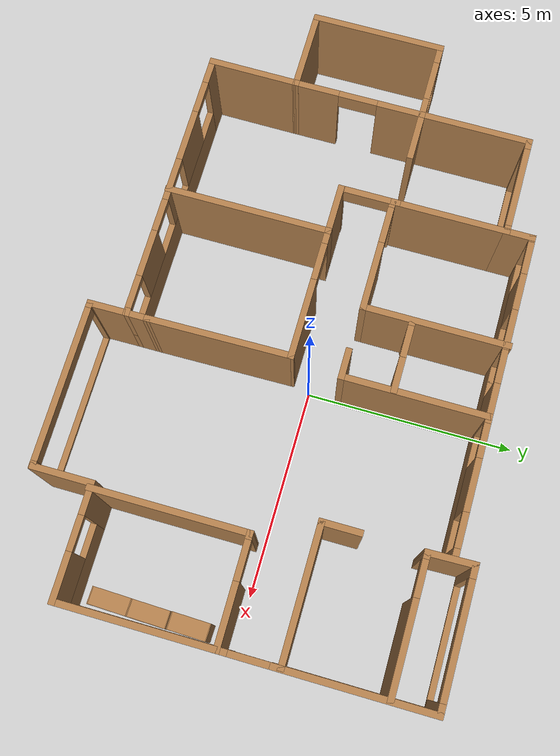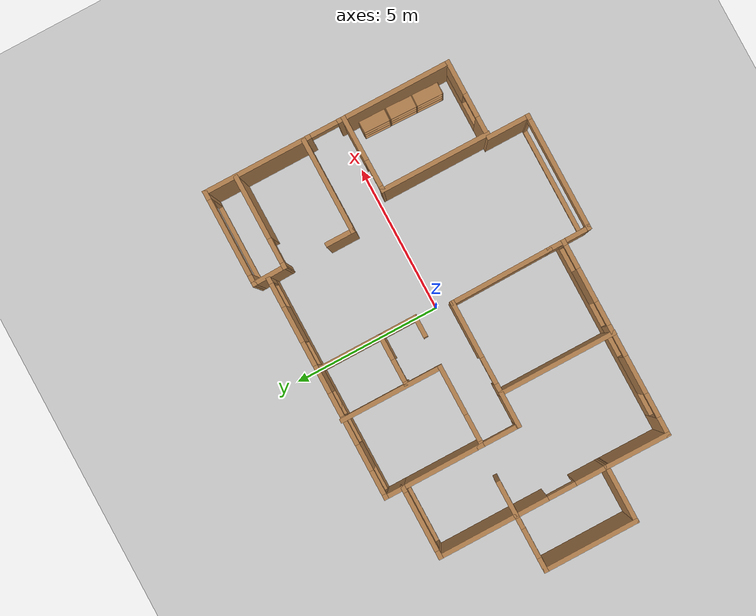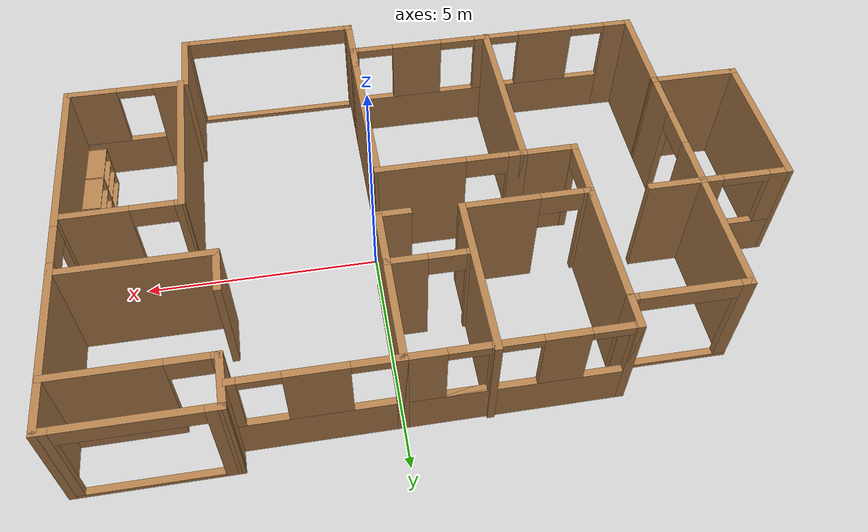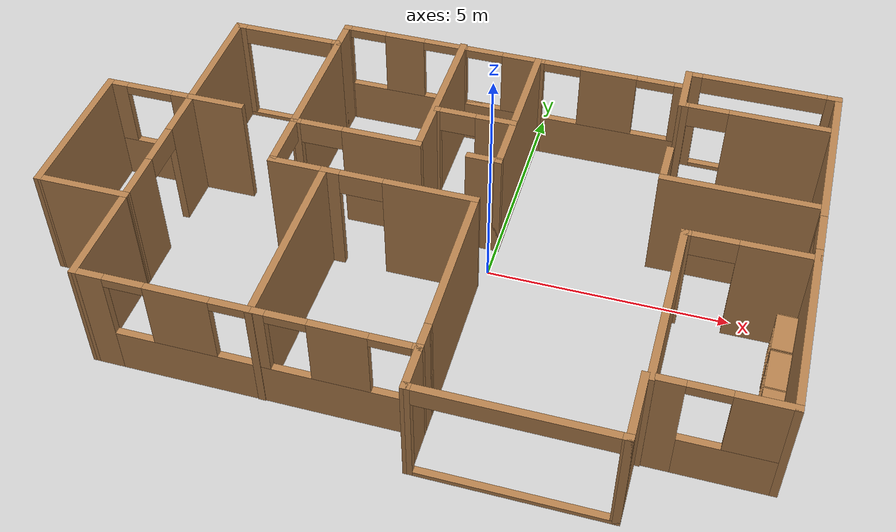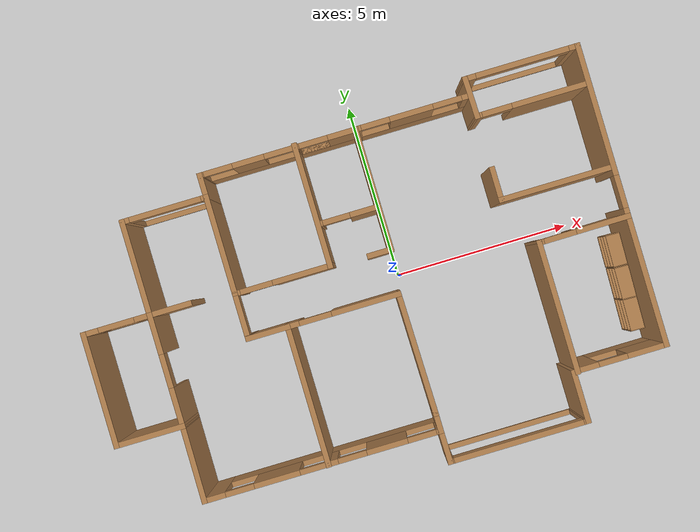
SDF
<sdf version="1.7">
 <world name="default">
  <light name="sun" type="directional">
   <pose>0 0 10 0 -0 0</pose>
   <diffuse>0.8 0.8 0.8 1</diffuse>
   <specular>0.2 0.2 0.2 1</specular>
   <attenuation>
    <range>1000</range>
    <constant>0.9</constant>
    <linear>0.01</linear>
    <quadratic>0.001</quadratic>
   </attenuation>
   <direction>-0.5 0.1 -0.9</direction>
   <spot><inner_angle>0</inner_angle><outer_angle>0</outer_angle><falloff>0</falloff></spot>
  </light>
  <model name="ground_plane">
   <static>1</static>
   <link name="link">
    <collision name="collision">
     <geometry><plane><normal>0 0 1</normal><size>100 100</size></plane></geometry>
     <surface>
      <contact><collide_bitmask>65535</collide_bitmask></contact>
      <friction><ode><mu>100</mu><mu2>50</mu2></ode></friction>
     </surface>
    </collision>
    <visual name="visual">
     <cast_shadows>0</cast_shadows>
     <geometry><plane><normal>0 0 1</normal><size>100 100</size></plane></geometry>
     <material>
      <script><uri>file://media/materials/scripts/gazebo.material</uri><name>Gazebo/Grey</name></script>
     </material>
    </visual>
   </link>
  </model>
  <gravity>0 0 -9.8</gravity>
  <magnetic_field>6e-06 2.3e-05 -4.2e-05</magnetic_field>
  <atmosphere type="adiabatic"/>
  <physics type="ode">
   <max_step_size>0.001</max_step_size>
   <real_time_factor>1</real_time_factor>
   <real_time_update_rate>1000</real_time_update_rate>
  </physics>
  <scene><ambient>0.4 0.4 0.4 1</ambient><background>0.7 0.7 0.7 1</background><shadows>1</shadows></scene>
  <spherical_coordinates>
   <surface_model>EARTH_WGS84</surface_model>
   <latitude_deg>0</latitude_deg>
   <longitude_deg>0</longitude_deg>
   <elevation>0</elevation>
   <heading_deg>0</heading_deg>
  </spherical_coordinates>
  <model name="home_1">
   <pose>-1.13065 -0.318162 0 0 -0 0</pose>
   <link name="Wall_1">
    <collision name="Wall_1_Collision">
     <geometry><box><size>3.25 0.15 2.5</size></box></geometry>
     <pose>0 0 1.25 0 -0 0</pose>
    </collision>
    <visual name="Wall_1_Visual">
     <pose>0 0 1.25 0 -0 0</pose>
     <geometry><box><size>3.25 0.15 2.5</size></box></geometry>
     <material>
      <script><uri>file://media/materials/scripts/gazebo.material</uri><name>Gazebo/Wood</name></script>
      <ambient>0.188235 0.188235 0.188235 1</ambient>
     </material>
     <meta><layer>0</layer></meta>
    </visual>
    <pose>-7.4437 -0.353578 0 0 -0 -1.5708</pose>
   </link>
   <link name="Wall_16">
    <collision name="Wall_16_Collision">
     <geometry><box><size>0.637 0.15 2.5</size></box></geometry>
     <pose>0 0 1.25 0 -0 0</pose>
    </collision>
    <visual name="Wall_16_Visual">
     <pose>0 0 1.25 0 -0 0</pose>
     <geometry><box><size>0.637 0.15 2.5</size></box></geometry>
     <material>
      <script><uri>file://media/materials/scripts/gazebo.material</uri><name>Gazebo/Wood</name></script>
      <ambient>1 1 1 1</ambient>
     </material>
     <meta><layer>0</layer></meta>
    </visual>
    <pose>0.998311 -3.74683 0 0 -0 1.5708</pose>
   </link>
   <link name="Wall_2">
    <collision name="Wall_2_Collision">
     <geometry><box><size>2 0.15 2.5</size></box></geometry>
     <pose>0 0 1.25 0 -0 0</pose>
    </collision>
    <visual name="Wall_2_Visual">
     <pose>0 0 1.25 0 -0 0</pose>
     <geometry><box><size>2 0.15 2.5</size></box></geometry>
     <material>
      <script><uri>file://media/materials/scripts/gazebo.material</uri><name>Gazebo/Wood</name></script>
      <ambient>0.188235 0.188235 0.188235 1</ambient>
     </material>
     <meta><layer>0</layer></meta>
    </visual>
    <pose>-6.51869 -1.90346 0 0 -0 0.000132</pose>
   </link>
   <link name="Wall_20">
    <pose>-5.59369 -0.353333 0 0 -0 1.5708</pose>
    <visual name="Wall_20_Visual_0">
     <pose>-1.05414 0 1.25 0 -0 0</pose>
     <geometry><box><size>1.14172 0.15 2.5</size></box></geometry>
     <material>
      <script><uri>file://media/materials/scripts/gazebo.material</uri><name>Gazebo/Wood</name></script>
      <ambient>0.188235 0.188235 0.188235 1</ambient>
     </material>
     <meta><layer>0</layer></meta>
    </visual>
    <collision name="Wall_20_Collision_0">
     <geometry><box><size>1.14172 0.15 2.5</size></box></geometry>
     <pose>-1.05414 0 1.25 0 -0 0</pose>
    </collision>
    <visual name="Wall_20_Visual_1">
     <pose>1.0407 0 1.25 0 -0 0</pose>
     <geometry><box><size>1.1686 0.15 2.5</size></box></geometry>
     <material>
      <script><uri>file://media/materials/scripts/gazebo.material</uri><name>Gazebo/Wood</name></script>
      <ambient>0.188235 0.188235 0.188235 1</ambient>
     </material>
     <meta><layer>0</layer></meta>
    </visual>
    <collision name="Wall_20_Collision_1">
     <geometry><box><size>1.1686 0.15 2.5</size></box></geometry>
     <pose>1.0407 0 1.25 0 -0 0</pose>
    </collision>
    <visual name="Wall_20_Visual_2">
     <pose>-0.01344 0 2.25 0 -0 0</pose>
     <geometry><box><size>0.939675 0.15 0.5</size></box></geometry>
     <material>
      <script><uri>file://media/materials/scripts/gazebo.material</uri><name>Gazebo/Wood</name></script>
      <ambient>0.188235 0.188235 0.188235 1</ambient>
     </material>
     <meta><layer>0</layer></meta>
    </visual>
    <collision name="Wall_20_Collision_2">
     <geometry><box><size>0.939675 0.15 0.5</size></box></geometry>
     <pose>-0.01344 0 2.25 0 -0 0</pose>
    </collision>
   </link>
   <link name="Wall_21">
    <pose>-6.51869 1.19654 0 0 -0 -3.14146</pose>
    <visual name="Wall_21_Visual_0">
     <pose>-0.744697 0 1.25 0 -0 0</pose>
     <geometry><box><size>0.510607 0.15 2.5</size></box></geometry>
     <material>
      <script><uri>file://media/materials/scripts/gazebo.material</uri><name>Gazebo/Wood</name></script>
      <ambient>0.188235 0.188235 0.188235 1</ambient>
     </material>
     <meta><layer>0</layer></meta>
    </visual>
    <collision name="Wall_21_Collision_0">
     <geometry><box><size>0.510607 0.15 2.5</size></box></geometry>
     <pose>-0.744697 0 1.25 0 -0 0</pose>
    </collision>
    <visual name="Wall_21_Visual_1">
     <pose>0.255303 0 0.5 0 -0 0</pose>
     <geometry><box><size>1.48939 0.15 1</size></box></geometry>
     <material>
      <script><uri>file://media/materials/scripts/gazebo.material</uri><name>Gazebo/Wood</name></script>
      <ambient>0.188235 0.188235 0.188235 1</ambient>
     </material>
     <meta><layer>0</layer></meta>
    </visual>
    <collision name="Wall_21_Collision_1">
     <geometry><box><size>1.48939 0.15 1</size></box></geometry>
     <pose>0.255303 0 0.5 0 -0 0</pose>
    </collision>
    <visual name="Wall_21_Visual_2">
     <pose>0.755303 0 1.75 0 -0 0</pose>
     <geometry><box><size>0.489393 0.15 1.5</size></box></geometry>
     <material>
      <script><uri>file://media/materials/scripts/gazebo.material</uri><name>Gazebo/Wood</name></script>
      <ambient>0.188235 0.188235 0.188235 1</ambient>
     </material>
     <meta><layer>0</layer></meta>
    </visual>
    <collision name="Wall_21_Collision_2">
     <geometry><box><size>0.489393 0.15 1.5</size></box></geometry>
     <pose>0.755303 0 1.75 0 -0 0</pose>
    </collision>
    <visual name="Wall_21_Visual_3">
     <pose>0.010607 0 2.4 0 -0 0</pose>
     <geometry><box><size>1 0.15 0.2</size></box></geometry>
     <material>
      <script><uri>file://media/materials/scripts/gazebo.material</uri><name>Gazebo/Wood</name></script>
      <ambient>0.188235 0.188235 0.188235 1</ambient>
     </material>
     <meta><layer>0</layer></meta>
    </visual>
    <collision name="Wall_21_Collision_3">
     <geometry><box><size>1 0.15 0.2</size></box></geometry>
     <pose>0.010607 0 2.4 0 -0 0</pose>
    </collision>
   </link>
   <link name="Wall_24">
    <collision name="Wall_24_Collision">
     <geometry><box><size>2.75 0.15 2.5</size></box></geometry>
     <pose>0 0 1.25 0 -0 0</pose>
    </collision>
    <visual name="Wall_24_Visual">
     <pose>0 0 1.25 0 -0 0</pose>
     <geometry><box><size>2.75 0.15 2.5</size></box></geometry>
     <material>
      <script><uri>file://media/materials/scripts/gazebo.material</uri><name>Gazebo/Wood</name></script>
      <ambient>1 1 1 1</ambient>
     </material>
     <meta><layer>0</layer></meta>
    </visual>
    <pose>-3.2437 2.49642 0 0 -0 1.5708</pose>
   </link>
   <link name="Wall_25">
    <pose>-4.4187 3.79642 0 0 -0 3.14159</pose>
    <visual name="Wall_25_Visual_0">
     <pose>-1.13657 0 1.25 0 -0 0</pose>
     <geometry><box><size>0.22686 0.15 2.5</size></box></geometry>
     <material>
      <script><uri>file://media/materials/scripts/gazebo.material</uri><name>Gazebo/Wood</name></script>
      <ambient>1 1 1 1</ambient>
     </material>
     <meta><layer>0</layer></meta>
    </visual>
    <collision name="Wall_25_Collision_0">
     <geometry><box><size>0.22686 0.15 2.5</size></box></geometry>
     <pose>-1.13657 0 1.25 0 -0 0</pose>
    </collision>
    <visual name="Wall_25_Visual_1">
     <pose>0.11343 0 0.05 0 -0 0</pose>
     <geometry><box><size>2.27314 0.15 0.1</size></box></geometry>
     <material>
      <script><uri>file://media/materials/scripts/gazebo.material</uri><name>Gazebo/Wood</name></script>
      <ambient>1 1 1 1</ambient>
     </material>
     <meta><layer>0</layer></meta>
    </visual>
    <collision name="Wall_25_Collision_1">
     <geometry><box><size>2.27314 0.15 0.1</size></box></geometry>
     <pose>0.11343 0 0.05 0 -0 0</pose>
    </collision>
    <visual name="Wall_25_Visual_2">
     <pose>1.11343 0 1.3 0 -0 0</pose>
     <geometry><box><size>0.27314 0.15 2.4</size></box></geometry>
     <material>
      <script><uri>file://media/materials/scripts/gazebo.material</uri><name>Gazebo/Wood</name></script>
      <ambient>1 1 1 1</ambient>
     </material>
     <meta><layer>0</layer></meta>
    </visual>
    <collision name="Wall_25_Collision_2">
     <geometry><box><size>0.27314 0.15 2.4</size></box></geometry>
     <pose>1.11343 0 1.3 0 -0 0</pose>
    </collision>
    <visual name="Wall_25_Visual_3">
     <pose>-0.02314 0 2.3 0 -0 0</pose>
     <geometry><box><size>2 0.15 0.4</size></box></geometry>
     <material>
      <script><uri>file://media/materials/scripts/gazebo.material</uri><name>Gazebo/Wood</name></script>
      <ambient>1 1 1 1</ambient>
     </material>
     <meta><layer>0</layer></meta>
    </visual>
    <collision name="Wall_25_Collision_3">
     <geometry><box><size>2 0.15 0.4</size></box></geometry>
     <pose>-0.02314 0 2.3 0 -0 0</pose>
    </collision>
   </link>
   <link name="Wall_26">
    <collision name="Wall_26_Collision">
     <geometry><box><size>2.74975 0.15 2.5</size></box></geometry>
     <pose>0 0 1.25 0 -0 0</pose>
    </collision>
    <visual name="Wall_26_Visual">
     <pose>0 0 1.25 0 -0 0</pose>
     <geometry><box><size>2.74975 0.15 2.5</size></box></geometry>
     <material>
      <script><uri>file://media/materials/scripts/gazebo.material</uri><name>Gazebo/Wood</name></script>
      <ambient>1 1 1 1</ambient>
     </material>
     <meta><layer>0</layer></meta>
    </visual>
    <pose>-5.59369 2.49654 0 0 -0 -1.57079</pose>
   </link>
   <link name="Wall_28">
    <pose>-3.2437 0.521422 0 0 -0 -1.5708</pose>
    <visual name="Wall_28_Visual_0">
     <pose>-0.634712 0 1.25 0 -0 0</pose>
     <geometry><box><size>0.230576 0.15 2.5</size></box></geometry>
     <material>
      <script><uri>file://media/materials/scripts/gazebo.material</uri><name>Gazebo/Wood</name></script>
      <ambient>1 1 1 1</ambient>
     </material>
     <meta><layer>0</layer></meta>
    </visual>
    <collision name="Wall_28_Collision_0">
     <geometry><box><size>0.230576 0.15 2.5</size></box></geometry>
     <pose>-0.634712 0 1.25 0 -0 0</pose>
    </collision>
    <visual name="Wall_28_Visual_1">
     <pose>0.670228 0 1.25 0 -0 0</pose>
     <geometry><box><size>0.159543 0.15 2.5</size></box></geometry>
     <material>
      <script><uri>file://media/materials/scripts/gazebo.material</uri><name>Gazebo/Wood</name></script>
      <ambient>1 1 1 1</ambient>
     </material>
     <meta><layer>0</layer></meta>
    </visual>
    <collision name="Wall_28_Collision_1">
     <geometry><box><size>0.159543 0.15 2.5</size></box></geometry>
     <pose>0.670228 0 1.25 0 -0 0</pose>
    </collision>
    <visual name="Wall_28_Visual_2">
     <pose>0.035516 0 2.25 0 -0 0</pose>
     <geometry><box><size>1.10988 0.15 0.5</size></box></geometry>
     <material>
      <script><uri>file://media/materials/scripts/gazebo.material</uri><name>Gazebo/Wood</name></script>
      <ambient>1 1 1 1</ambient>
     </material>
     <meta><layer>0</layer></meta>
    </visual>
    <collision name="Wall_28_Collision_2">
     <geometry><box><size>1.10988 0.15 0.5</size></box></geometry>
     <pose>0.035516 0 2.25 0 -0 0</pose>
    </collision>
   </link>
   <link name="Wall_29">
    <collision name="Wall_29_Collision">
     <geometry><box><size>1.25 0.15 2.5</size></box></geometry>
     <pose>0 0 1.25 0 -0 0</pose>
    </collision>
    <visual name="Wall_29_Visual">
     <pose>0 0 1.25 0 -0 0</pose>
     <geometry><box><size>1.25 0.15 2.5</size></box></geometry>
     <material>
      <script><uri>file://media/materials/scripts/gazebo.material</uri><name>Gazebo/Wood</name></script>
      <ambient>1 1 1 1</ambient>
     </material>
     <meta><layer>0</layer></meta>
    </visual>
    <pose>-2.6937 -0.153578 0 0 -0 0</pose>
   </link>
   <link name="Wall_3">
    <collision name="Wall_3_Collision">
     <geometry><box><size>2.23704 0.15 2.5</size></box></geometry>
     <pose>0 0 1.25 0 -0 0</pose>
    </collision>
    <visual name="Wall_3_Visual">
     <pose>0 0 1.25 0 -0 0</pose>
     <geometry><box><size>2.23704 0.15 2.5</size></box></geometry>
     <material>
      <script><uri>file://media/materials/scripts/gazebo.material</uri><name>Gazebo/Wood</name></script>
      <ambient>1 1 1 1</ambient>
     </material>
     <meta><layer>0</layer></meta>
    </visual>
    <pose>-5.60019 -2.94683 0 0 -0 -1.57702</pose>
   </link>
   <link name="Wall_31">
    <collision name="Wall_31_Collision">
     <geometry><box><size>4 0.15 2.5</size></box></geometry>
     <pose>0 0 1.25 0 -0 0</pose>
    </collision>
    <visual name="Wall_31_Visual">
     <pose>0 0 1.25 0 -0 0</pose>
     <geometry><box><size>4 0.15 2.5</size></box></geometry>
     <material>
      <script><uri>file://media/materials/scripts/gazebo.material</uri><name>Gazebo/Wood</name></script>
      <ambient>1 1 1 1</ambient>
     </material>
     <meta><layer>0</layer></meta>
    </visual>
    <pose>-2.1437 -2.07858 0 0 -0 -1.5708</pose>
   </link>
   <link name="Wall_33">
    <pose>-0.593697 -0.153578 0 0 -0 0</pose>
    <visual name="Wall_33_Visual_0">
     <pose>-1.42431 0 1.25 0 -0 0</pose>
     <geometry><box><size>0.401373 0.15 2.5</size></box></geometry>
     <material>
      <script><uri>file://media/materials/scripts/gazebo.material</uri><name>Gazebo/Wood</name></script>
      <ambient>1 1 1 1</ambient>
     </material>
     <meta><layer>0</layer></meta>
    </visual>
    <collision name="Wall_33_Collision_0">
     <geometry><box><size>0.401373 0.15 2.5</size></box></geometry>
     <pose>-1.42431 0 1.25 0 -0 0</pose>
    </collision>
    <visual name="Wall_33_Visual_1">
     <pose>0.650686 0 1.25 0 -0 0</pose>
     <geometry><box><size>1.94863 0.15 2.5</size></box></geometry>
     <material>
      <script><uri>file://media/materials/scripts/gazebo.material</uri><name>Gazebo/Wood</name></script>
      <ambient>1 1 1 1</ambient>
     </material>
     <meta><layer>0</layer></meta>
    </visual>
    <collision name="Wall_33_Collision_1">
     <geometry><box><size>1.94863 0.15 2.5</size></box></geometry>
     <pose>0.650686 0 1.25 0 -0 0</pose>
    </collision>
    <visual name="Wall_33_Visual_2">
     <pose>-0.773627 0 2.25 0 -0 0</pose>
     <geometry><box><size>0.9 0.15 0.5</size></box></geometry>
     <material>
      <script><uri>file://media/materials/scripts/gazebo.material</uri><name>Gazebo/Wood</name></script>
      <ambient>1 1 1 1</ambient>
     </material>
     <meta><layer>0</layer></meta>
    </visual>
    <collision name="Wall_33_Collision_2">
     <geometry><box><size>0.9 0.15 0.5</size></box></geometry>
     <pose>-0.773627 0 2.25 0 -0 0</pose>
    </collision>
   </link>
   <link name="Wall_34">
    <collision name="Wall_34_Collision">
     <geometry><box><size>3.50002 0.15 2.5</size></box></geometry>
     <pose>0 0 1.25 0 -0 0</pose>
    </collision>
    <visual name="Wall_34_Visual">
     <pose>0 0 1.25 0 -0 0</pose>
     <geometry><box><size>3.50002 0.15 2.5</size></box></geometry>
     <material>
      <script><uri>file://media/materials/scripts/gazebo.material</uri><name>Gazebo/Wood</name></script>
      <ambient>1 1 1 1</ambient>
     </material>
     <meta><layer>0</layer></meta>
    </visual>
    <pose>0.977307 -1.82846 0 0 -0 -1.55826</pose>
   </link>
   <link name="Wall_36">
    <collision name="Wall_36_Collision">
     <geometry><box><size>3.75 0.15 2.5</size></box></geometry>
     <pose>0 0 1.25 0 -0 0</pose>
    </collision>
    <visual name="Wall_36_Visual">
     <pose>0 0 1.25 0 -0 0</pose>
     <geometry><box><size>3.75 0.15 2.5</size></box></geometry>
     <material>
      <script><uri>file://media/materials/scripts/gazebo.material</uri><name>Gazebo/Wood</name></script>
      <ambient>1 1 1 1</ambient>
     </material>
     <meta><layer>0</layer></meta>
    </visual>
    <pose>4.96022 -1.71642 0 0 -0 -1.57085</pose>
   </link>
   <link name="Wall_38">
    <pose>6.20181 0.090167 0 0 -0 0.005236</pose>
    <visual name="Wall_38_Visual_0">
     <pose>-1.21235 0 1.25 0 -0 0</pose>
     <geometry><box><size>0.208334 0.15 2.5</size></box></geometry>
     <material>
      <script><uri>file://media/materials/scripts/gazebo.material</uri><name>Gazebo/Wood</name></script>
      <ambient>1 1 1 1</ambient>
     </material>
     <meta><layer>0</layer></meta>
    </visual>
    <collision name="Wall_38_Collision_0">
     <geometry><box><size>0.208334 0.15 2.5</size></box></geometry>
     <pose>-1.21235 0 1.25 0 -0 0</pose>
    </collision>
    <visual name="Wall_38_Visual_1">
     <pose>0.554167 0 1.25 0 -0 0</pose>
     <geometry><box><size>1.5247 0.15 2.5</size></box></geometry>
     <material>
      <script><uri>file://media/materials/scripts/gazebo.material</uri><name>Gazebo/Wood</name></script>
      <ambient>1 1 1 1</ambient>
     </material>
     <meta><layer>0</layer></meta>
    </visual>
    <collision name="Wall_38_Collision_1">
     <geometry><box><size>1.5247 0.15 2.5</size></box></geometry>
     <pose>0.554167 0 1.25 0 -0 0</pose>
    </collision>
    <visual name="Wall_38_Visual_2">
     <pose>-0.658183 0 2.25 0 -0 0</pose>
     <geometry><box><size>0.9 0.15 0.5</size></box></geometry>
     <material>
      <script><uri>file://media/materials/scripts/gazebo.material</uri><name>Gazebo/Wood</name></script>
      <ambient>1 1 1 1</ambient>
     </material>
     <meta><layer>0</layer></meta>
    </visual>
    <collision name="Wall_38_Collision_2">
     <geometry><box><size>0.9 0.15 0.5</size></box></geometry>
     <pose>-0.658183 0 2.25 0 -0 0</pose>
    </collision>
   </link>
   <link name="Wall_4">
    <pose>-2.30419 -3.99033 0 0 -0 0</pose>
    <visual name="Wall_4_Visual_0">
     <pose>-3.04337 0 1.25 0 -0 0</pose>
     <geometry><box><size>0.668937 0.15 2.5</size></box></geometry>
     <material>
      <script><uri>file://media/materials/scripts/gazebo.material</uri><name>Gazebo/Wood</name></script>
      <ambient>1 1 1 1</ambient>
     </material>
     <meta><layer>0</layer></meta>
    </visual>
    <collision name="Wall_4_Collision_0">
     <geometry><box><size>0.668937 0.15 2.5</size></box></geometry>
     <pose>-3.04337 0 1.25 0 -0 0</pose>
    </collision>
    <visual name="Wall_4_Visual_1">
     <pose>0.334469 0 0.5 0 -0 0</pose>
     <geometry><box><size>6.08674 0.15 1</size></box></geometry>
     <material>
      <script><uri>file://media/materials/scripts/gazebo.material</uri><name>Gazebo/Wood</name></script>
      <ambient>1 1 1 1</ambient>
     </material>
     <meta><layer>0</layer></meta>
    </visual>
    <collision name="Wall_4_Collision_1">
     <geometry><box><size>6.08674 0.15 1</size></box></geometry>
     <pose>0.334469 0 0.5 0 -0 0</pose>
    </collision>
    <visual name="Wall_4_Visual_2">
     <pose>-1.26803 0 1.75 0 -0 0</pose>
     <geometry><box><size>1.28175 0.15 1.5</size></box></geometry>
     <material>
      <script><uri>file://media/materials/scripts/gazebo.material</uri><name>Gazebo/Wood</name></script>
      <ambient>1 1 1 1</ambient>
     </material>
     <meta><layer>0</layer></meta>
    </visual>
    <collision name="Wall_4_Collision_2">
     <geometry><box><size>1.28175 0.15 1.5</size></box></geometry>
     <pose>-1.26803 0 1.75 0 -0 0</pose>
    </collision>
    <visual name="Wall_4_Visual_3">
     <pose>0.304856 0 1.75 0 -0 0</pose>
     <geometry><box><size>0.264008 0.15 1.5</size></box></geometry>
     <material>
      <script><uri>file://media/materials/scripts/gazebo.material</uri><name>Gazebo/Wood</name></script>
      <ambient>1 1 1 1</ambient>
     </material>
     <meta><layer>0</layer></meta>
    </visual>
    <collision name="Wall_4_Collision_3">
     <geometry><box><size>0.264008 0.15 1.5</size></box></geometry>
     <pose>0.304856 0 1.75 0 -0 0</pose>
    </collision>
    <visual name="Wall_4_Visual_4">
     <pose>1.80835 0 1.75 0 -0 0</pose>
     <geometry><box><size>1.14297 0.15 1.5</size></box></geometry>
     <material>
      <script><uri>file://media/materials/scripts/gazebo.material</uri><name>Gazebo/Wood</name></script>
      <ambient>1 1 1 1</ambient>
     </material>
     <meta><layer>0</layer></meta>
    </visual>
    <collision name="Wall_4_Collision_4">
     <geometry><box><size>1.14297 0.15 1.5</size></box></geometry>
     <pose>1.80835 0 1.75 0 -0 0</pose>
    </collision>
    <visual name="Wall_4_Visual_5">
     <pose>3.27884 0 1.75 0 -0 0</pose>
     <geometry><box><size>0.19801 0.15 1.5</size></box></geometry>
     <material>
      <script><uri>file://media/materials/scripts/gazebo.material</uri><name>Gazebo/Wood</name></script>
      <ambient>1 1 1 1</ambient>
     </material>
     <meta><layer>0</layer></meta>
    </visual>
    <collision name="Wall_4_Collision_5">
     <geometry><box><size>0.19801 0.15 1.5</size></box></geometry>
     <pose>3.27884 0 1.75 0 -0 0</pose>
    </collision>
    <visual name="Wall_4_Visual_6">
     <pose>-2.3089 0 2.4 0 -0 0</pose>
     <geometry><box><size>0.8 0.15 0.2</size></box></geometry>
     <material>
      <script><uri>file://media/materials/scripts/gazebo.material</uri><name>Gazebo/Wood</name></script>
      <ambient>1 1 1 1</ambient>
     </material>
     <meta><layer>0</layer></meta>
    </visual>
    <collision name="Wall_4_Collision_6">
     <geometry><box><size>0.8 0.15 0.2</size></box></geometry>
     <pose>-2.3089 0 2.4 0 -0 0</pose>
    </collision>
    <visual name="Wall_4_Visual_7">
     <pose>-0.227149 0 2.4 0 -0 0</pose>
     <geometry><box><size>0.8 0.15 0.2</size></box></geometry>
     <material>
      <script><uri>file://media/materials/scripts/gazebo.material</uri><name>Gazebo/Wood</name></script>
      <ambient>1 1 1 1</ambient>
     </material>
     <meta><layer>0</layer></meta>
    </visual>
    <collision name="Wall_4_Collision_7">
     <geometry><box><size>0.8 0.15 0.2</size></box></geometry>
     <pose>-0.227149 0 2.4 0 -0 0</pose>
    </collision>
    <visual name="Wall_4_Visual_8">
     <pose>0.83686 0 2.4 0 -0 0</pose>
     <geometry><box><size>0.8 0.15 0.2</size></box></geometry>
     <material>
      <script><uri>file://media/materials/scripts/gazebo.material</uri><name>Gazebo/Wood</name></script>
      <ambient>1 1 1 1</ambient>
     </material>
     <meta><layer>0</layer></meta>
    </visual>
    <collision name="Wall_4_Collision_8">
     <geometry><box><size>0.8 0.15 0.2</size></box></geometry>
     <pose>0.83686 0 2.4 0 -0 0</pose>
    </collision>
    <visual name="Wall_4_Visual_9">
     <pose>2.77983 0 2.4 0 -0 0</pose>
     <geometry><box><size>0.8 0.15 0.2</size></box></geometry>
     <material>
      <script><uri>file://media/materials/scripts/gazebo.material</uri><name>Gazebo/Wood</name></script>
      <ambient>1 1 1 1</ambient>
     </material>
     <meta><layer>0</layer></meta>
    </visual>
    <collision name="Wall_4_Collision_9">
     <geometry><box><size>0.8 0.15 0.2</size></box></geometry>
     <pose>2.77983 0 2.4 0 -0 0</pose>
    </collision>
   </link>
   <link name="Wall_40">
    <collision name="Wall_40_Collision">
     <geometry><box><size>0.75 0.15 2.5</size></box></geometry>
     <pose>0 0 1.25 0 -0 0</pose>
    </collision>
    <visual name="Wall_40_Visual">
     <pose>0 0 1.25 0 -0 0</pose>
     <geometry><box><size>0.75 0.15 2.5</size></box></geometry>
     <material>
      <script><uri>file://media/materials/scripts/gazebo.material</uri><name>Gazebo/Wood</name></script>
      <ambient>1 1 1 1</ambient>
     </material>
     <meta><layer>0</layer></meta>
    </visual>
    <pose>-3.2437 4.09642 0 0 -0 1.5708</pose>
   </link>
   <link name="Wall_41">
    <pose>-1.0687 4.39642 0 0 -0 0</pose>
    <visual name="Wall_41_Visual_0">
     <pose>-2.16041 0 1.25 0 -0 0</pose>
     <geometry><box><size>0.179184 0.15 2.5</size></box></geometry>
     <material>
      <script><uri>file://media/materials/scripts/gazebo.material</uri><name>Gazebo/Wood</name></script>
      <ambient>1 1 1 1</ambient>
     </material>
     <meta><layer>0</layer></meta>
    </visual>
    <collision name="Wall_41_Collision_0">
     <geometry><box><size>0.179184 0.15 2.5</size></box></geometry>
     <pose>-2.16041 0 1.25 0 -0 0</pose>
    </collision>
    <visual name="Wall_41_Visual_1">
     <pose>0.089592 0 0.5 0 -0 0</pose>
     <geometry><box><size>4.32082 0.15 1</size></box></geometry>
     <material>
      <script><uri>file://media/materials/scripts/gazebo.material</uri><name>Gazebo/Wood</name></script>
      <ambient>1 1 1 1</ambient>
     </material>
     <meta><layer>0</layer></meta>
    </visual>
    <collision name="Wall_41_Collision_1">
     <geometry><box><size>4.32082 0.15 1</size></box></geometry>
     <pose>0.089592 0 0.5 0 -0 0</pose>
    </collision>
    <visual name="Wall_41_Visual_2">
     <pose>-0.826549 0 1.75 0 -0 0</pose>
     <geometry><box><size>0.888534 0.15 1.5</size></box></geometry>
     <material>
      <script><uri>file://media/materials/scripts/gazebo.material</uri><name>Gazebo/Wood</name></script>
      <ambient>1 1 1 1</ambient>
     </material>
     <meta><layer>0</layer></meta>
    </visual>
    <collision name="Wall_41_Collision_2">
     <geometry><box><size>0.888534 0.15 1.5</size></box></geometry>
     <pose>-0.826549 0 1.75 0 -0 0</pose>
    </collision>
    <visual name="Wall_41_Visual_3">
     <pose>0.503461 0 1.75 0 -0 0</pose>
     <geometry><box><size>0.171485 0.15 1.5</size></box></geometry>
     <material>
      <script><uri>file://media/materials/scripts/gazebo.material</uri><name>Gazebo/Wood</name></script>
      <ambient>1 1 1 1</ambient>
     </material>
     <meta><layer>0</layer></meta>
    </visual>
    <collision name="Wall_41_Collision_3">
     <geometry><box><size>0.171485 0.15 1.5</size></box></geometry>
     <pose>0.503461 0 1.75 0 -0 0</pose>
    </collision>
    <visual name="Wall_41_Visual_4">
     <pose>1.8196 0 1.75 0 -0 0</pose>
     <geometry><box><size>0.860796 0.15 1.5</size></box></geometry>
     <material>
      <script><uri>file://media/materials/scripts/gazebo.material</uri><name>Gazebo/Wood</name></script>
      <ambient>1 1 1 1</ambient>
     </material>
     <meta><layer>0</layer></meta>
    </visual>
    <collision name="Wall_41_Collision_4">
     <geometry><box><size>0.860796 0.15 1.5</size></box></geometry>
     <pose>1.8196 0 1.75 0 -0 0</pose>
    </collision>
    <visual name="Wall_41_Visual_5">
     <pose>0.989204 0 1 0 -0 0</pose>
     <geometry><box><size>0.8 0.15 0</size></box></geometry>
     <material>
      <script><uri>file://media/materials/scripts/gazebo.material</uri><name>Gazebo/Wood</name></script>
      <ambient>1 1 1 1</ambient>
     </material>
     <meta><layer>0</layer></meta>
    </visual>
    <collision name="Wall_41_Collision_5">
     <geometry><box><size>0.8 0.15 0</size></box></geometry>
     <pose>0.989204 0 1 0 -0 0</pose>
    </collision>
    <visual name="Wall_41_Visual_6">
     <pose>-1.67082 0 2.4 0 -0 0</pose>
     <geometry><box><size>0.8 0.15 0.2</size></box></geometry>
     <material>
      <script><uri>file://media/materials/scripts/gazebo.material</uri><name>Gazebo/Wood</name></script>
      <ambient>1 1 1 1</ambient>
     </material>
     <meta><layer>0</layer></meta>
    </visual>
    <collision name="Wall_41_Collision_6">
     <geometry><box><size>0.8 0.15 0.2</size></box></geometry>
     <pose>-1.67082 0 2.4 0 -0 0</pose>
    </collision>
    <visual name="Wall_41_Visual_7">
     <pose>0.017718 0 2.4 0 -0 0</pose>
     <geometry><box><size>0.8 0.15 0.2</size></box></geometry>
     <material>
      <script><uri>file://media/materials/scripts/gazebo.material</uri><name>Gazebo/Wood</name></script>
      <ambient>1 1 1 1</ambient>
     </material>
     <meta><layer>0</layer></meta>
    </visual>
    <collision name="Wall_41_Collision_7">
     <geometry><box><size>0.8 0.15 0.2</size></box></geometry>
     <pose>0.017718 0 2.4 0 -0 0</pose>
    </collision>
    <visual name="Wall_41_Visual_8">
     <pose>0.989204 0 2.4 0 -0 0</pose>
     <geometry><box><size>0.8 0.15 0.2</size></box></geometry>
     <material>
      <script><uri>file://media/materials/scripts/gazebo.material</uri><name>Gazebo/Wood</name></script>
      <ambient>1 1 1 1</ambient>
     </material>
     <meta><layer>0</layer></meta>
    </visual>
    <collision name="Wall_41_Collision_8">
     <geometry><box><size>0.8 0.15 0.2</size></box></geometry>
     <pose>0.989204 0 2.4 0 -0 0</pose>
    </collision>
   </link>
   <link name="Wall_42">
    <collision name="Wall_42_Collision">
     <geometry><box><size>3.5 0.15 2.5</size></box></geometry>
     <pose>0 0 1.25 0 -0 0</pose>
    </collision>
    <visual name="Wall_42_Visual">
     <pose>0 0 1.25 0 -0 0</pose>
     <geometry><box><size>3.5 0.15 2.5</size></box></geometry>
     <material>
      <script><uri>file://media/materials/scripts/gazebo.material</uri><name>Gazebo/Wood</name></script>
      <ambient>0.188235 0.188235 0.188235 1</ambient>
     </material>
     <meta><layer>0</layer></meta>
    </visual>
    <pose>1.1063 2.72142 0 0 -0 -1.5708</pose>
   </link>
   <link name="Wall_43">
    <collision name="Wall_43_Collision">
     <geometry><box><size>0.75 0.15 2.5</size></box></geometry>
     <pose>0 0 1.25 0 -0 0</pose>
    </collision>
    <visual name="Wall_43_Visual">
     <pose>0 0 1.25 0 -0 0</pose>
     <geometry><box><size>0.75 0.15 2.5</size></box></geometry>
     <material>
      <script><uri>file://media/materials/scripts/gazebo.material</uri><name>Gazebo/Wood</name></script>
      <ambient>1 1 1 1</ambient>
     </material>
     <meta><layer>0</layer></meta>
    </visual>
    <pose>0.806303 1.04642 0 0 -0 3.14159</pose>
   </link>
   <link name="Wall_45">
    <collision name="Wall_45_Collision">
     <geometry><box><size>3.5 0.15 2.5</size></box></geometry>
     <pose>0 0 1.25 0 -0 0</pose>
    </collision>
    <visual name="Wall_45_Visual">
     <pose>0 0 1.25 0 -0 0</pose>
     <geometry><box><size>3.5 0.15 2.5</size></box></geometry>
     <material>
      <script><uri>file://media/materials/scripts/gazebo.material</uri><name>Gazebo/Wood</name></script>
      <ambient>0.188235 0.188235 0.188235 1</ambient>
     </material>
     <meta><layer>0</layer></meta>
    </visual>
    <pose>-0.586575 2.7685 0 0 -0 -1.5708</pose>
   </link>
   <link name="Wall_46">
    <pose>-1.88657 1.0935 0 0 -0 3.14159</pose>
    <visual name="Wall_46_Visual_0">
     <pose>-0.532292 0 1.25 0 -0 0</pose>
     <geometry><box><size>1.68542 0.15 2.5</size></box></geometry>
     <material>
      <script><uri>file://media/materials/scripts/gazebo.material</uri><name>Gazebo/Wood</name></script>
      <ambient>1 1 1 1</ambient>
     </material>
     <meta><layer>0</layer></meta>
    </visual>
    <collision name="Wall_46_Collision_0">
     <geometry><box><size>1.68542 0.15 2.5</size></box></geometry>
     <pose>-0.532292 0 1.25 0 -0 0</pose>
    </collision>
    <visual name="Wall_46_Visual_1">
     <pose>1.29271 0 1.25 0 -0 0</pose>
     <geometry><box><size>0.164584 0.15 2.5</size></box></geometry>
     <material>
      <script><uri>file://media/materials/scripts/gazebo.material</uri><name>Gazebo/Wood</name></script>
      <ambient>1 1 1 1</ambient>
     </material>
     <meta><layer>0</layer></meta>
    </visual>
    <collision name="Wall_46_Collision_1">
     <geometry><box><size>0.164584 0.15 2.5</size></box></geometry>
     <pose>1.29271 0 1.25 0 -0 0</pose>
    </collision>
    <visual name="Wall_46_Visual_2">
     <pose>0.760416 0 2.25 0 -0 0</pose>
     <geometry><box><size>0.9 0.15 0.5</size></box></geometry>
     <material>
      <script><uri>file://media/materials/scripts/gazebo.material</uri><name>Gazebo/Wood</name></script>
      <ambient>1 1 1 1</ambient>
     </material>
     <meta><layer>0</layer></meta>
    </visual>
    <collision name="Wall_46_Collision_2">
     <geometry><box><size>0.9 0.15 0.5</size></box></geometry>
     <pose>0.760416 0 2.25 0 -0 0</pose>
    </collision>
   </link>
   <link name="Wall_48">
    <pose>0.293425 2.24349 0 0 -0 0</pose>
    <visual name="Wall_48_Visual_0">
     <pose>-0.810522 0 1.25 0 -0 0</pose>
     <geometry><box><size>0.128956 0.15 2.5</size></box></geometry>
     <material>
      <script><uri>file://media/materials/scripts/gazebo.material</uri><name>Gazebo/Wood</name></script>
      <ambient>0.188235 0.188235 0.188235 1</ambient>
     </material>
     <meta><layer>0</layer></meta>
    </visual>
    <collision name="Wall_48_Collision_0">
     <geometry><box><size>0.128956 0.15 2.5</size></box></geometry>
     <pose>-0.810522 0 1.25 0 -0 0</pose>
    </collision>
    <visual name="Wall_48_Visual_1">
     <pose>0.444518 0 1.25 0 -0 0</pose>
     <geometry><box><size>0.860964 0.15 2.5</size></box></geometry>
     <material>
      <script><uri>file://media/materials/scripts/gazebo.material</uri><name>Gazebo/Wood</name></script>
      <ambient>0.188235 0.188235 0.188235 1</ambient>
     </material>
     <meta><layer>0</layer></meta>
    </visual>
    <collision name="Wall_48_Collision_1">
     <geometry><box><size>0.860964 0.15 2.5</size></box></geometry>
     <pose>0.444518 0 1.25 0 -0 0</pose>
    </collision>
    <visual name="Wall_48_Visual_2">
     <pose>-0.366004 0 2.25 0 -0 0</pose>
     <geometry><box><size>0.76008 0.15 0.5</size></box></geometry>
     <material>
      <script><uri>file://media/materials/scripts/gazebo.material</uri><name>Gazebo/Wood</name></script>
      <ambient>0.188235 0.188235 0.188235 1</ambient>
     </material>
     <meta><layer>0</layer></meta>
    </visual>
    <collision name="Wall_48_Collision_2">
     <geometry><box><size>0.76008 0.15 0.5</size></box></geometry>
     <pose>-0.366004 0 2.25 0 -0 0</pose>
    </collision>
   </link>
   <link name="Wall_5">
    <collision name="Wall_5_Collision">
     <geometry><box><size>1.01328 0.15 2.5</size></box></geometry>
     <pose>0 0 1.25 0 -0 0</pose>
    </collision>
    <visual name="Wall_5_Visual">
     <pose>0 0 1.25 0 -0 0</pose>
     <geometry><box><size>1.01328 0.15 2.5</size></box></geometry>
     <material>
      <script><uri>file://media/materials/scripts/gazebo.material</uri><name>Gazebo/Wood</name></script>
      <ambient>1 1 1 1</ambient>
     </material>
     <meta><layer>0</layer></meta>
    </visual>
    <pose>1.00231 -4.42196 0 0 -0 -1.56154</pose>
   </link>
   <link name="Wall_50">
    <pose>2.6563 4.39642 0 0 -0 0</pose>
    <visual name="Wall_50_Visual_0">
     <pose>-1.513 0 1.25 0 -0 0</pose>
     <geometry><box><size>0.223999 0.15 2.5</size></box></geometry>
     <material>
      <script><uri>file://media/materials/scripts/gazebo.material</uri><name>Gazebo/Wood</name></script>
      <ambient>1 1 1 1</ambient>
     </material>
     <meta><layer>0</layer></meta>
    </visual>
    <collision name="Wall_50_Collision_0">
     <geometry><box><size>0.223999 0.15 2.5</size></box></geometry>
     <pose>-1.513 0 1.25 0 -0 0</pose>
    </collision>
    <visual name="Wall_50_Visual_1">
     <pose>0.112 0 0.5 0 -0 0</pose>
     <geometry><box><size>3.026 0.15 1</size></box></geometry>
     <material>
      <script><uri>file://media/materials/scripts/gazebo.material</uri><name>Gazebo/Wood</name></script>
      <ambient>1 1 1 1</ambient>
     </material>
     <meta><layer>0</layer></meta>
    </visual>
    <collision name="Wall_50_Collision_1">
     <geometry><box><size>3.026 0.15 1</size></box></geometry>
     <pose>0.112 0 0.5 0 -0 0</pose>
    </collision>
    <visual name="Wall_50_Visual_2">
     <pose>0.00518 0 1.75 0 -0 0</pose>
     <geometry><box><size>1.21236 0.15 1.5</size></box></geometry>
     <material>
      <script><uri>file://media/materials/scripts/gazebo.material</uri><name>Gazebo/Wood</name></script>
      <ambient>1 1 1 1</ambient>
     </material>
     <meta><layer>0</layer></meta>
    </visual>
    <collision name="Wall_50_Collision_2">
     <geometry><box><size>1.21236 0.15 1.5</size></box></geometry>
     <pose>0.00518 0 1.75 0 -0 0</pose>
    </collision>
    <visual name="Wall_50_Visual_3">
     <pose>1.51818 0 1.75 0 -0 0</pose>
     <geometry><box><size>0.213638 0.15 1.5</size></box></geometry>
     <material>
      <script><uri>file://media/materials/scripts/gazebo.material</uri><name>Gazebo/Wood</name></script>
      <ambient>1 1 1 1</ambient>
     </material>
     <meta><layer>0</layer></meta>
    </visual>
    <collision name="Wall_50_Collision_3">
     <geometry><box><size>0.213638 0.15 1.5</size></box></geometry>
     <pose>1.51818 0 1.75 0 -0 0</pose>
    </collision>
    <visual name="Wall_50_Visual_4">
     <pose>-1.001 0 2.4 0 -0 0</pose>
     <geometry><box><size>0.8 0.15 0.2</size></box></geometry>
     <material>
      <script><uri>file://media/materials/scripts/gazebo.material</uri><name>Gazebo/Wood</name></script>
      <ambient>1 1 1 1</ambient>
     </material>
     <meta><layer>0</layer></meta>
    </visual>
    <collision name="Wall_50_Collision_4">
     <geometry><box><size>0.8 0.15 0.2</size></box></geometry>
     <pose>-1.001 0 2.4 0 -0 0</pose>
    </collision>
    <visual name="Wall_50_Visual_5">
     <pose>1.01136 0 2.4 0 -0 0</pose>
     <geometry><box><size>0.8 0.15 0.2</size></box></geometry>
     <material>
      <script><uri>file://media/materials/scripts/gazebo.material</uri><name>Gazebo/Wood</name></script>
      <ambient>1 1 1 1</ambient>
     </material>
     <meta><layer>0</layer></meta>
    </visual>
    <collision name="Wall_50_Collision_5">
     <geometry><box><size>0.8 0.15 0.2</size></box></geometry>
     <pose>1.01136 0 2.4 0 -0 0</pose>
    </collision>
   </link>
   <link name="Wall_6">
    <pose>2.9313 -4.85358 0 0 -0 0</pose>
    <visual name="Wall_6_Visual_0">
     <pose>-1.90855 0 1.25 0 -0 0</pose>
     <geometry><box><size>0.182893 0.15 2.5</size></box></geometry>
     <material>
      <script><uri>file://media/materials/scripts/gazebo.material</uri><name>Gazebo/Wood</name></script>
      <ambient>1 1 1 1</ambient>
     </material>
     <meta><layer>0</layer></meta>
    </visual>
    <collision name="Wall_6_Collision_0">
     <geometry><box><size>0.182893 0.15 2.5</size></box></geometry>
     <pose>-1.90855 0 1.25 0 -0 0</pose>
    </collision>
    <visual name="Wall_6_Visual_1">
     <pose>0.091447 0 0.05 0 -0 0</pose>
     <geometry><box><size>3.81711 0.15 0.1</size></box></geometry>
     <material>
      <script><uri>file://media/materials/scripts/gazebo.material</uri><name>Gazebo/Wood</name></script>
      <ambient>1 1 1 1</ambient>
     </material>
     <meta><layer>0</layer></meta>
    </visual>
    <collision name="Wall_6_Collision_1">
     <geometry><box><size>3.81711 0.15 0.1</size></box></geometry>
     <pose>0.091447 0 0.05 0 -0 0</pose>
    </collision>
    <visual name="Wall_6_Visual_2">
     <pose>1.90348 0 1.3 0 -0 0</pose>
     <geometry><box><size>0.193045 0.15 2.4</size></box></geometry>
     <material>
      <script><uri>file://media/materials/scripts/gazebo.material</uri><name>Gazebo/Wood</name></script>
      <ambient>1 1 1 1</ambient>
     </material>
     <meta><layer>0</layer></meta>
    </visual>
    <collision name="Wall_6_Collision_2">
     <geometry><box><size>0.193045 0.15 2.4</size></box></geometry>
     <pose>1.90348 0 1.3 0 -0 0</pose>
    </collision>
    <visual name="Wall_6_Visual_3">
     <pose>-0.005076 0 2.3 0 -0 0</pose>
     <geometry><box><size>3.62406 0.15 0.4</size></box></geometry>
     <material>
      <script><uri>file://media/materials/scripts/gazebo.material</uri><name>Gazebo/Wood</name></script>
      <ambient>1 1 1 1</ambient>
     </material>
     <meta><layer>0</layer></meta>
    </visual>
    <collision name="Wall_6_Collision_3">
     <geometry><box><size>3.62406 0.15 0.4</size></box></geometry>
     <pose>-0.005076 0 2.3 0 -0 0</pose>
    </collision>
   </link>
   <link name="Wall_62">
    <pose>7.44331 0.681167 0 0 -0 1.5708</pose>
    <visual name="Wall_62_Visual_0">
     <pose>-2.30071 0 1.25 0 -0 0</pose>
     <geometry><box><size>3.89159 0.15 2.5</size></box></geometry>
     <material>
      <script><uri>file://media/materials/scripts/gazebo.material</uri><name>Gazebo/Wood</name></script>
      <ambient>1 1 1 1</ambient>
     </material>
     <meta><layer>0</layer></meta>
    </visual>
    <collision name="Wall_62_Collision_0">
     <geometry><box><size>3.89159 0.15 2.5</size></box></geometry>
     <pose>-2.30071 0 1.25 0 -0 0</pose>
    </collision>
    <visual name="Wall_62_Visual_1">
     <pose>2.40241 0 1.25 0 -0 0</pose>
     <geometry><box><size>3.68819 0.15 2.5</size></box></geometry>
     <material>
      <script><uri>file://media/materials/scripts/gazebo.material</uri><name>Gazebo/Wood</name></script>
      <ambient>1 1 1 1</ambient>
     </material>
     <meta><layer>0</layer></meta>
    </visual>
    <collision name="Wall_62_Collision_1">
     <geometry><box><size>3.68819 0.15 2.5</size></box></geometry>
     <pose>2.40241 0 1.25 0 -0 0</pose>
    </collision>
    <visual name="Wall_62_Visual_2">
     <pose>0.101699 0 2.25 0 -0 0</pose>
     <geometry><box><size>0.913225 0.15 0.5</size></box></geometry>
     <material>
      <script><uri>file://media/materials/scripts/gazebo.material</uri><name>Gazebo/Wood</name></script>
      <ambient>1 1 1 1</ambient>
     </material>
     <meta><layer>0</layer></meta>
    </visual>
    <collision name="Wall_62_Collision_2">
     <geometry><box><size>0.913225 0.15 0.5</size></box></geometry>
     <pose>0.101699 0 2.25 0 -0 0</pose>
    </collision>
   </link>
   <link name="Wall_64">
    <pose>5.87244 4.85261 0 0 -0 3.7e-05</pose>
    <visual name="Wall_64_Visual_0">
     <pose>-1.461 0 1.25 0 -0 0</pose>
     <geometry><box><size>0.369747 0.15 2.5</size></box></geometry>
     <material>
      <script><uri>file://media/materials/scripts/gazebo.material</uri><name>Gazebo/Wood</name></script>
      <ambient>1 1 1 1</ambient>
     </material>
     <meta><layer>0</layer></meta>
    </visual>
    <collision name="Wall_64_Collision_0">
     <geometry><box><size>0.369747 0.15 2.5</size></box></geometry>
     <pose>-1.461 0 1.25 0 -0 0</pose>
    </collision>
    <visual name="Wall_64_Visual_1">
     <pose>0.184873 0 0.05 0 -0 0</pose>
     <geometry><box><size>2.922 0.15 0.1</size></box></geometry>
     <material>
      <script><uri>file://media/materials/scripts/gazebo.material</uri><name>Gazebo/Wood</name></script>
      <ambient>1 1 1 1</ambient>
     </material>
     <meta><layer>0</layer></meta>
    </visual>
    <collision name="Wall_64_Collision_1">
     <geometry><box><size>2.922 0.15 0.1</size></box></geometry>
     <pose>0.184873 0 0.05 0 -0 0</pose>
    </collision>
    <visual name="Wall_64_Visual_2">
     <pose>1.48487 0 1.3 0 -0 0</pose>
     <geometry><box><size>0.322001 0.15 2.4</size></box></geometry>
     <material>
      <script><uri>file://media/materials/scripts/gazebo.material</uri><name>Gazebo/Wood</name></script>
      <ambient>1 1 1 1</ambient>
     </material>
     <meta><layer>0</layer></meta>
    </visual>
    <collision name="Wall_64_Collision_2">
     <geometry><box><size>0.322001 0.15 2.4</size></box></geometry>
     <pose>1.48487 0 1.3 0 -0 0</pose>
    </collision>
    <visual name="Wall_64_Visual_3">
     <pose>0.023873 0 2.3 0 -0 0</pose>
     <geometry><box><size>2.6 0.15 0.4</size></box></geometry>
     <material>
      <script><uri>file://media/materials/scripts/gazebo.material</uri><name>Gazebo/Wood</name></script>
      <ambient>1 1 1 1</ambient>
     </material>
     <meta><layer>0</layer></meta>
    </visual>
    <collision name="Wall_64_Collision_3">
     <geometry><box><size>2.6 0.15 0.4</size></box></geometry>
     <pose>0.023873 0 2.3 0 -0 0</pose>
    </collision>
   </link>
   <link name="Wall_68">
    <pose>5.87572 3.81139 0 0 -0 0</pose>
    <visual name="Wall_68_Visual_0">
     <pose>-1.51824 0 1.25 0 -0 0</pose>
     <geometry><box><size>0.213513 0.15 2.5</size></box></geometry>
     <material>
      <script><uri>file://media/materials/scripts/gazebo.material</uri><name>Gazebo/Wood</name></script>
      <ambient>0.333333 0.341176 0.32549 1</ambient>
     </material>
     <meta><layer>0</layer></meta>
    </visual>
    <collision name="Wall_68_Collision_0">
     <geometry><box><size>0.213513 0.15 2.5</size></box></geometry>
     <pose>-1.51824 0 1.25 0 -0 0</pose>
    </collision>
    <visual name="Wall_68_Visual_1">
     <pose>0.523694 0 1.25 0 -0 0</pose>
     <geometry><box><size>2.20261 0.15 2.5</size></box></geometry>
     <material>
      <script><uri>file://media/materials/scripts/gazebo.material</uri><name>Gazebo/Wood</name></script>
      <ambient>0.333333 0.341176 0.32549 1</ambient>
     </material>
     <meta><layer>0</layer></meta>
    </visual>
    <collision name="Wall_68_Collision_1">
     <geometry><box><size>2.20261 0.15 2.5</size></box></geometry>
     <pose>0.523694 0 1.25 0 -0 0</pose>
    </collision>
    <visual name="Wall_68_Visual_2">
     <pose>-0.99455 0 2.25 0 -0 0</pose>
     <geometry><box><size>0.833875 0.15 0.5</size></box></geometry>
     <material>
      <script><uri>file://media/materials/scripts/gazebo.material</uri><name>Gazebo/Wood</name></script>
      <ambient>0.333333 0.341176 0.32549 1</ambient>
     </material>
     <meta><layer>0</layer></meta>
    </visual>
    <collision name="Wall_68_Collision_2">
     <geometry><box><size>0.833875 0.15 0.5</size></box></geometry>
     <pose>-0.99455 0 2.25 0 -0 0</pose>
    </collision>
   </link>
   <link name="Wall_70">
    <collision name="Wall_70_Collision">
     <geometry><box><size>1.19144 0.15 2.5</size></box></geometry>
     <pose>0 0 1.25 0 -0 0</pose>
    </collision>
    <visual name="Wall_70_Visual">
     <pose>0 0 1.25 0 -0 0</pose>
     <geometry><box><size>1.19144 0.15 2.5</size></box></geometry>
     <material>
      <script><uri>file://media/materials/scripts/gazebo.material</uri><name>Gazebo/Wood</name></script>
      <ambient>1 1 1 1</ambient>
     </material>
     <meta><layer>0</layer></meta>
    </visual>
    <pose>4.31364 4.33197 0 0 -0 -1.5476</pose>
   </link>
   <link name="Wall_72">
    <collision name="Wall_72_Collision">
     <geometry><box><size>1 0.15 2.5</size></box></geometry>
     <pose>0 0 1.25 0 -0 0</pose>
    </collision>
    <visual name="Wall_72_Visual">
     <pose>0 0 1.25 0 -0 0</pose>
     <geometry><box><size>1 0.15 2.5</size></box></geometry>
     <material>
      <script><uri>file://media/materials/scripts/gazebo.material</uri><name>Gazebo/Wood</name></script>
      <ambient>0.188235 0.188235 0.188235 1</ambient>
     </material>
     <meta><layer>0</layer></meta>
    </visual>
    <pose>4.31249 1.90519 0 0 -0 -1.5708</pose>
   </link>
   <link name="Wall_73">
    <collision name="Wall_73_Collision">
     <geometry><box><size>3.25 0.15 2.5</size></box></geometry>
     <pose>0 0 1.25 0 -0 0</pose>
    </collision>
    <visual name="Wall_73_Visual">
     <pose>0 0 1.25 0 -0 0</pose>
     <geometry><box><size>3.25 0.15 2.5</size></box></geometry>
     <material>
      <script><uri>file://media/materials/scripts/gazebo.material</uri><name>Gazebo/Wood</name></script>
      <ambient>0.333333 0.341176 0.32549 1</ambient>
     </material>
     <meta><layer>0</layer></meta>
    </visual>
    <pose>5.86249 1.48019 0 0 -0 0</pose>
   </link>
   <link name="Wall_75">
    <collision name="Wall_75_Collision">
     <geometry><box><size>1.5 0.15 2.5</size></box></geometry>
     <pose>0 0 1.25 0 -0 0</pose>
    </collision>
    <visual name="Wall_75_Visual">
     <pose>0 0 1.25 0 -0 0</pose>
     <geometry><box><size>1.5 0.15 2.5</size></box></geometry>
     <material>
      <script><uri>file://media/materials/scripts/gazebo.material</uri><name>Gazebo/Wood</name></script>
      <ambient>1 1 1 1</ambient>
     </material>
     <meta><layer>0</layer></meta>
    </visual>
    <pose>4.8563 -4.17858 0 0 -0 1.5708</pose>
   </link>
   <link name="Wall_77">
    <collision name="Wall_77_Collision">
     <geometry><box><size>1.25 0.15 2.5</size></box></geometry>
     <pose>0 0 1.25 0 -0 0</pose>
    </collision>
    <visual name="Wall_77_Visual">
     <pose>0 0 1.25 0 -0 0</pose>
     <geometry><box><size>1.25 0.15 2.5</size></box></geometry>
     <material>
      <script><uri>file://media/materials/scripts/gazebo.material</uri><name>Gazebo/Wood</name></script>
      <ambient>1 1 1 1</ambient>
     </material>
     <meta><layer>0</layer></meta>
    </visual>
    <pose>-5.04369 1.19654 0 0 -0 -0.000223</pose>
   </link>
   <link name="Wall_8">
    <pose>6.26831 -3.49033 0 0 -0 0</pose>
    <visual name="Wall_8_Visual_0">
     <pose>-0.9771 0 1.25 0 -0 0</pose>
     <geometry><box><size>0.5458 0.15 2.5</size></box></geometry>
     <material>
      <script><uri>file://media/materials/scripts/gazebo.material</uri><name>Gazebo/Wood</name></script>
      <ambient>1 1 1 1</ambient>
     </material>
     <meta><layer>0</layer></meta>
    </visual>
    <collision name="Wall_8_Collision_0">
     <geometry><box><size>0.5458 0.15 2.5</size></box></geometry>
     <pose>-0.9771 0 1.25 0 -0 0</pose>
    </collision>
    <visual name="Wall_8_Visual_1">
     <pose>0.2729 0 0.5 0 -0 0</pose>
     <geometry><box><size>1.9542 0.15 1</size></box></geometry>
     <material>
      <script><uri>file://media/materials/scripts/gazebo.material</uri><name>Gazebo/Wood</name></script>
      <ambient>1 1 1 1</ambient>
     </material>
     <meta><layer>0</layer></meta>
    </visual>
    <collision name="Wall_8_Collision_1">
     <geometry><box><size>1.9542 0.15 1</size></box></geometry>
     <pose>0.2729 0 0.5 0 -0 0</pose>
    </collision>
    <visual name="Wall_8_Visual_2">
     <pose>0.6729 0 1.75 0 -0 0</pose>
     <geometry><box><size>1.1542 0.15 1.5</size></box></geometry>
     <material>
      <script><uri>file://media/materials/scripts/gazebo.material</uri><name>Gazebo/Wood</name></script>
      <ambient>1 1 1 1</ambient>
     </material>
     <meta><layer>0</layer></meta>
    </visual>
    <collision name="Wall_8_Collision_2">
     <geometry><box><size>1.1542 0.15 1.5</size></box></geometry>
     <pose>0.6729 0 1.75 0 -0 0</pose>
    </collision>
    <visual name="Wall_8_Visual_3">
     <pose>-0.3042 0 2.4 0 -0 0</pose>
     <geometry><box><size>0.8 0.15 0.2</size></box></geometry>
     <material>
      <script><uri>file://media/materials/scripts/gazebo.material</uri><name>Gazebo/Wood</name></script>
      <ambient>1 1 1 1</ambient>
     </material>
     <meta><layer>0</layer></meta>
    </visual>
    <collision name="Wall_8_Collision_3">
     <geometry><box><size>0.8 0.15 0.2</size></box></geometry>
     <pose>-0.3042 0 2.4 0 -0 0</pose>
    </collision>
   </link>
   <static>1</static>
  </model>
  <model name="Bookshelf_clone">
   <static>1</static>
   <link name="link">
    <inertial><mass>1</mass></inertial>
    <collision name="back">
     <pose>0 0.005 0.6 0 -0 0</pose>
     <geometry><box><size>0.9 0.01 1.2</size></box></geometry>
    </collision>
    <visual name="visual1">
     <pose>0 0.005 0.6 0 -0 0</pose>
     <geometry><box><size>0.9 0.01 1.2</size></box></geometry>
     <material>
      <diffuse>1 1 1 1</diffuse>
      <script><uri>file://media/materials/scripts/gazebo.material</uri><name>Gazebo/Wood</name></script>
      <pbr>
       <metal>
        <albedo_map>https://fuel.ignitionrobotics.org/1.0/openrobotics/models/bookshelf/3/files/bookshelf_diffuse.jpg</albedo_map>
       </metal>
      </pbr>
     </material>
    </visual>
    <collision name="left_side">
     <pose>0.45 -0.195 0.6 0 -0 0</pose>
     <geometry><box><size>0.02 0.4 1.2</size></box></geometry>
    </collision>
    <visual name="visual2">
     <pose>0.45 -0.195 0.6 0 -0 0</pose>
     <geometry><box><size>0.02 0.4 1.2</size></box></geometry>
     <material>
      <diffuse>1 1 1 1</diffuse>
      <script><uri>file://media/materials/scripts/gazebo.material</uri><name>Gazebo/Wood</name></script>
      <pbr>
       <metal>
        <albedo_map>https://fuel.ignitionrobotics.org/1.0/openrobotics/models/bookshelf/3/files/bookshelf_diffuse.jpg</albedo_map>
       </metal>
      </pbr>
     </material>
    </visual>
    <collision name="right_side">
     <pose>-0.45 -0.195 0.6 0 -0 0</pose>
     <geometry><box><size>0.02 0.4 1.2</size></box></geometry>
    </collision>
    <visual name="visual3">
     <pose>-0.45 -0.195 0.6 0 -0 0</pose>
     <geometry><box><size>0.02 0.4 1.2</size></box></geometry>
     <material>
      <diffuse>1 1 1 1</diffuse>
      <script><uri>file://media/materials/scripts/gazebo.material</uri><name>Gazebo/Wood</name></script>
      <pbr>
       <metal>
        <albedo_map>https://fuel.ignitionrobotics.org/1.0/openrobotics/models/bookshelf/3/files/bookshelf_diffuse.jpg</albedo_map>
       </metal>
      </pbr>
     </material>
    </visual>
    <collision name="bottom">
     <pose>0 -0.195 0.03 0 -0 0</pose>
     <geometry><box><size>0.88 0.4 0.06</size></box></geometry>
    </collision>
    <visual name="visual4">
     <pose>0 -0.195 0.03 0 -0 0</pose>
     <geometry><box><size>0.88 0.4 0.06</size></box></geometry>
     <material>
      <diffuse>1 1 1 1</diffuse>
      <script><uri>file://media/materials/scripts/gazebo.material</uri><name>Gazebo/Wood</name></script>
      <pbr>
       <metal>
        <albedo_map>https://fuel.ignitionrobotics.org/1.0/openrobotics/models/bookshelf/3/files/bookshelf_diffuse.jpg</albedo_map>
       </metal>
      </pbr>
     </material>
    </visual>
    <collision name="top">
     <pose>0 -0.195 1.19 0 -0 0</pose>
     <geometry><box><size>0.88 0.4 0.02</size></box></geometry>
    </collision>
    <visual name="visual5">
     <pose>0 -0.195 1.19 0 -0 0</pose>
     <geometry><box><size>0.88 0.4 0.02</size></box></geometry>
     <material>
      <diffuse>1 1 1 1</diffuse>
      <script><uri>file://media/materials/scripts/gazebo.material</uri><name>Gazebo/Wood</name></script>
      <pbr>
       <metal>
        <albedo_map>https://fuel.ignitionrobotics.org/1.0/openrobotics/models/bookshelf/3/files/bookshelf_diffuse.jpg</albedo_map>
       </metal>
      </pbr>
     </material>
    </visual>
    <collision name="low_shelf">
     <pose>0 -0.195 0.43 0 -0 0</pose>
     <geometry><box><size>0.88 0.4 0.02</size></box></geometry>
    </collision>
    <visual name="visual6">
     <pose>0 -0.195 0.43 0 -0 0</pose>
     <geometry><box><size>0.88 0.4 0.02</size></box></geometry>
     <material>
      <diffuse>1 1 1 1</diffuse>
      <script><uri>file://media/materials/scripts/gazebo.material</uri><name>Gazebo/Wood</name></script>
      <pbr>
       <metal>
        <albedo_map>https://fuel.ignitionrobotics.org/1.0/openrobotics/models/bookshelf/3/files/bookshelf_diffuse.jpg</albedo_map>
       </metal>
      </pbr>
     </material>
    </visual>
    <collision name="high_shelf">
     <pose>0 -0.195 0.8 0 -0 0</pose>
     <geometry><box><size>0.88 0.4 0.02</size></box></geometry>
    </collision>
    <visual name="visual7">
     <pose>0 -0.195 0.8 0 -0 0</pose>
     <geometry><box><size>0.88 0.4 0.02</size></box></geometry>
     <material>
      <diffuse>1 1 1 1</diffuse>
      <script><uri>file://media/materials/scripts/gazebo.material</uri><name>Gazebo/Wood</name></script>
      <pbr>
       <metal>
        <albedo_map>https://fuel.ignitionrobotics.org/1.0/openrobotics/models/bookshelf/3/files/bookshelf_diffuse.jpg</albedo_map>
       </metal>
      </pbr>
     </material>
    </visual>
   </link>
   <pose>6.2046 -1.05208 0 0 0 -1.5962</pose>
  </model>
  <model name="Bookshelf_clone_clone">
   <static>1</static>
   <link name="link">
    <inertial><mass>1</mass></inertial>
    <collision name="back">
     <pose>0 0.005 0.6 0 -0 0</pose>
     <geometry><box><size>0.9 0.01 1.2</size></box></geometry>
    </collision>
    <visual name="visual1">
     <pose>0 0.005 0.6 0 -0 0</pose>
     <geometry><box><size>0.9 0.01 1.2</size></box></geometry>
     <material>
      <diffuse>1 1 1 1</diffuse>
      <script><uri>file://media/materials/scripts/gazebo.material</uri><name>Gazebo/Wood</name></script>
      <pbr>
       <metal>
        <albedo_map>https://fuel.ignitionrobotics.org/1.0/openrobotics/models/bookshelf/3/files/bookshelf_diffuse.jpg</albedo_map>
       </metal>
      </pbr>
     </material>
    </visual>
    <collision name="left_side">
     <pose>0.45 -0.195 0.6 0 -0 0</pose>
     <geometry><box><size>0.02 0.4 1.2</size></box></geometry>
    </collision>
    <visual name="visual2">
     <pose>0.45 -0.195 0.6 0 -0 0</pose>
     <geometry><box><size>0.02 0.4 1.2</size></box></geometry>
     <material>
      <diffuse>1 1 1 1</diffuse>
      <script><uri>file://media/materials/scripts/gazebo.material</uri><name>Gazebo/Wood</name></script>
      <pbr>
       <metal>
        <albedo_map>https://fuel.ignitionrobotics.org/1.0/openrobotics/models/bookshelf/3/files/bookshelf_diffuse.jpg</albedo_map>
       </metal>
      </pbr>
     </material>
    </visual>
    <collision name="right_side">
     <pose>-0.45 -0.195 0.6 0 -0 0</pose>
     <geometry><box><size>0.02 0.4 1.2</size></box></geometry>
    </collision>
    <visual name="visual3">
     <pose>-0.45 -0.195 0.6 0 -0 0</pose>
     <geometry><box><size>0.02 0.4 1.2</size></box></geometry>
     <material>
      <diffuse>1 1 1 1</diffuse>
      <script><uri>file://media/materials/scripts/gazebo.material</uri><name>Gazebo/Wood</name></script>
      <pbr>
       <metal>
        <albedo_map>https://fuel.ignitionrobotics.org/1.0/openrobotics/models/bookshelf/3/files/bookshelf_diffuse.jpg</albedo_map>
       </metal>
      </pbr>
     </material>
    </visual>
    <collision name="bottom">
     <pose>0 -0.195 0.03 0 -0 0</pose>
     <geometry><box><size>0.88 0.4 0.06</size></box></geometry>
    </collision>
    <visual name="visual4">
     <pose>0 -0.195 0.03 0 -0 0</pose>
     <geometry><box><size>0.88 0.4 0.06</size></box></geometry>
     <material>
      <diffuse>1 1 1 1</diffuse>
      <script><uri>file://media/materials/scripts/gazebo.material</uri><name>Gazebo/Wood</name></script>
      <pbr>
       <metal>
        <albedo_map>https://fuel.ignitionrobotics.org/1.0/openrobotics/models/bookshelf/3/files/bookshelf_diffuse.jpg</albedo_map>
       </metal>
      </pbr>
     </material>
    </visual>
    <collision name="top">
     <pose>0 -0.195 1.19 0 -0 0</pose>
     <geometry><box><size>0.88 0.4 0.02</size></box></geometry>
    </collision>
    <visual name="visual5">
     <pose>0 -0.195 1.19 0 -0 0</pose>
     <geometry><box><size>0.88 0.4 0.02</size></box></geometry>
     <material>
      <diffuse>1 1 1 1</diffuse>
      <script><uri>file://media/materials/scripts/gazebo.material</uri><name>Gazebo/Wood</name></script>
      <pbr>
       <metal>
        <albedo_map>https://fuel.ignitionrobotics.org/1.0/openrobotics/models/bookshelf/3/files/bookshelf_diffuse.jpg</albedo_map>
       </metal>
      </pbr>
     </material>
    </visual>
    <collision name="low_shelf">
     <pose>0 -0.195 0.43 0 -0 0</pose>
     <geometry><box><size>0.88 0.4 0.02</size></box></geometry>
    </collision>
    <visual name="visual6">
     <pose>0 -0.195 0.43 0 -0 0</pose>
     <geometry><box><size>0.88 0.4 0.02</size></box></geometry>
     <material>
      <diffuse>1 1 1 1</diffuse>
      <script><uri>file://media/materials/scripts/gazebo.material</uri><name>Gazebo/Wood</name></script>
      <pbr>
       <metal>
        <albedo_map>https://fuel.ignitionrobotics.org/1.0/openrobotics/models/bookshelf/3/files/bookshelf_diffuse.jpg</albedo_map>
       </metal>
      </pbr>
     </material>
    </visual>
    <collision name="high_shelf">
     <pose>0 -0.195 0.8 0 -0 0</pose>
     <geometry><box><size>0.88 0.4 0.02</size></box></geometry>
    </collision>
    <visual name="visual7">
     <pose>0 -0.195 0.8 0 -0 0</pose>
     <geometry><box><size>0.88 0.4 0.02</size></box></geometry>
     <material>
      <diffuse>1 1 1 1</diffuse>
      <script><uri>file://media/materials/scripts/gazebo.material</uri><name>Gazebo/Wood</name></script>
      <pbr>
       <metal>
        <albedo_map>https://fuel.ignitionrobotics.org/1.0/openrobotics/models/bookshelf/3/files/bookshelf_diffuse.jpg</albedo_map>
       </metal>
      </pbr>
     </material>
    </visual>
   </link>
   <pose>6.18658 -1.98511 0 0 0 -1.5962</pose>
  </model>
  <model name="Bookshelf_clone_clone_0">
   <static>1</static>
   <link name="link">
    <inertial><mass>1</mass></inertial>
    <collision name="back">
     <pose>0 0.005 0.6 0 -0 0</pose>
     <geometry><box><size>0.9 0.01 1.2</size></box></geometry>
    </collision>
    <visual name="visual1">
     <pose>0 0.005 0.6 0 -0 0</pose>
     <geometry><box><size>0.9 0.01 1.2</size></box></geometry>
     <material>
      <diffuse>1 1 1 1</diffuse>
      <script><uri>file://media/materials/scripts/gazebo.material</uri><name>Gazebo/Wood</name></script>
      <pbr>
       <metal>
        <albedo_map>https://fuel.ignitionrobotics.org/1.0/openrobotics/models/bookshelf/3/files/bookshelf_diffuse.jpg</albedo_map>
       </metal>
      </pbr>
     </material>
    </visual>
    <collision name="left_side">
     <pose>0.45 -0.195 0.6 0 -0 0</pose>
     <geometry><box><size>0.02 0.4 1.2</size></box></geometry>
    </collision>
    <visual name="visual2">
     <pose>0.45 -0.195 0.6 0 -0 0</pose>
     <geometry><box><size>0.02 0.4 1.2</size></box></geometry>
     <material>
      <diffuse>1 1 1 1</diffuse>
      <script><uri>file://media/materials/scripts/gazebo.material</uri><name>Gazebo/Wood</name></script>
      <pbr>
       <metal>
        <albedo_map>https://fuel.ignitionrobotics.org/1.0/openrobotics/models/bookshelf/3/files/bookshelf_diffuse.jpg</albedo_map>
       </metal>
      </pbr>
     </material>
    </visual>
    <collision name="right_side">
     <pose>-0.45 -0.195 0.6 0 -0 0</pose>
     <geometry><box><size>0.02 0.4 1.2</size></box></geometry>
    </collision>
    <visual name="visual3">
     <pose>-0.45 -0.195 0.6 0 -0 0</pose>
     <geometry><box><size>0.02 0.4 1.2</size></box></geometry>
     <material>
      <diffuse>1 1 1 1</diffuse>
      <script><uri>file://media/materials/scripts/gazebo.material</uri><name>Gazebo/Wood</name></script>
      <pbr>
       <metal>
        <albedo_map>https://fuel.ignitionrobotics.org/1.0/openrobotics/models/bookshelf/3/files/bookshelf_diffuse.jpg</albedo_map>
       </metal>
      </pbr>
     </material>
    </visual>
    <collision name="bottom">
     <pose>0 -0.195 0.03 0 -0 0</pose>
     <geometry><box><size>0.88 0.4 0.06</size></box></geometry>
    </collision>
    <visual name="visual4">
     <pose>0 -0.195 0.03 0 -0 0</pose>
     <geometry><box><size>0.88 0.4 0.06</size></box></geometry>
     <material>
      <diffuse>1 1 1 1</diffuse>
      <script><uri>file://media/materials/scripts/gazebo.material</uri><name>Gazebo/Wood</name></script>
      <pbr>
       <metal>
        <albedo_map>https://fuel.ignitionrobotics.org/1.0/openrobotics/models/bookshelf/3/files/bookshelf_diffuse.jpg</albedo_map>
       </metal>
      </pbr>
     </material>
    </visual>
    <collision name="top">
     <pose>0 -0.195 1.19 0 -0 0</pose>
     <geometry><box><size>0.88 0.4 0.02</size></box></geometry>
    </collision>
    <visual name="visual5">
     <pose>0 -0.195 1.19 0 -0 0</pose>
     <geometry><box><size>0.88 0.4 0.02</size></box></geometry>
     <material>
      <diffuse>1 1 1 1</diffuse>
      <script><uri>file://media/materials/scripts/gazebo.material</uri><name>Gazebo/Wood</name></script>
      <pbr>
       <metal>
        <albedo_map>https://fuel.ignitionrobotics.org/1.0/openrobotics/models/bookshelf/3/files/bookshelf_diffuse.jpg</albedo_map>
       </metal>
      </pbr>
     </material>
    </visual>
    <collision name="low_shelf">
     <pose>0 -0.195 0.43 0 -0 0</pose>
     <geometry><box><size>0.88 0.4 0.02</size></box></geometry>
    </collision>
    <visual name="visual6">
     <pose>0 -0.195 0.43 0 -0 0</pose>
     <geometry><box><size>0.88 0.4 0.02</size></box></geometry>
     <material>
      <diffuse>1 1 1 1</diffuse>
      <script><uri>file://media/materials/scripts/gazebo.material</uri><name>Gazebo/Wood</name></script>
      <pbr>
       <metal>
        <albedo_map>https://fuel.ignitionrobotics.org/1.0/openrobotics/models/bookshelf/3/files/bookshelf_diffuse.jpg</albedo_map>
       </metal>
      </pbr>
     </material>
    </visual>
    <collision name="high_shelf">
     <pose>0 -0.195 0.8 0 -0 0</pose>
     <geometry><box><size>0.88 0.4 0.02</size></box></geometry>
    </collision>
    <visual name="visual7">
     <pose>0 -0.195 0.8 0 -0 0</pose>
     <geometry><box><size>0.88 0.4 0.02</size></box></geometry>
     <material>
      <diffuse>1 1 1 1</diffuse>
      <script><uri>file://media/materials/scripts/gazebo.material</uri><name>Gazebo/Wood</name></script>
      <pbr>
       <metal>
        <albedo_map>https://fuel.ignitionrobotics.org/1.0/openrobotics/models/bookshelf/3/files/bookshelf_diffuse.jpg</albedo_map>
       </metal>
      </pbr>
     </material>
    </visual>
   </link>
   <pose>6.16097 -2.89816 0 0 0 -1.5962</pose>
  </model>
 </world>
</sdf>
